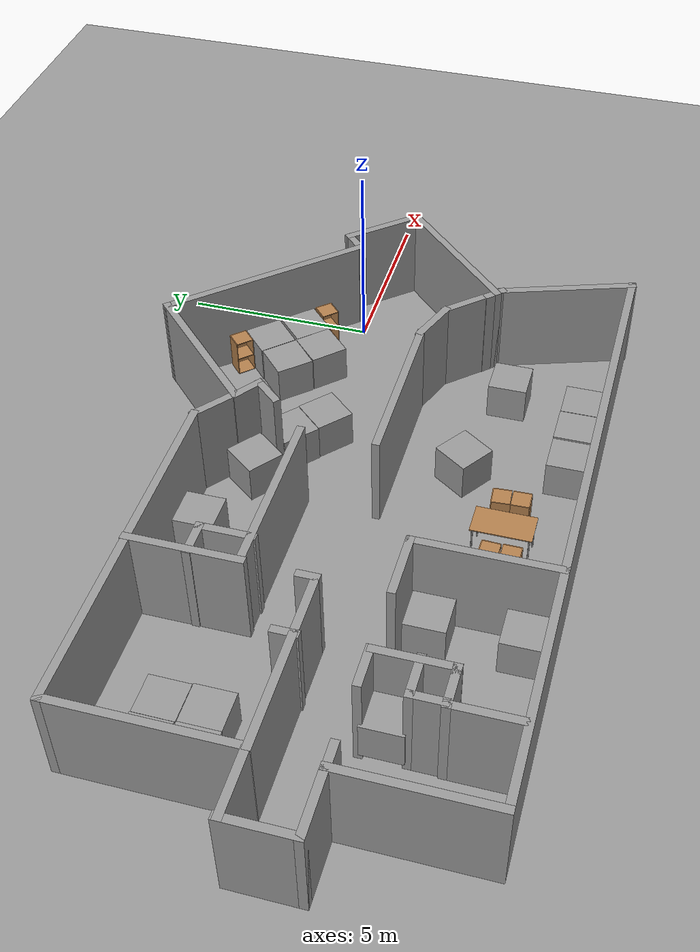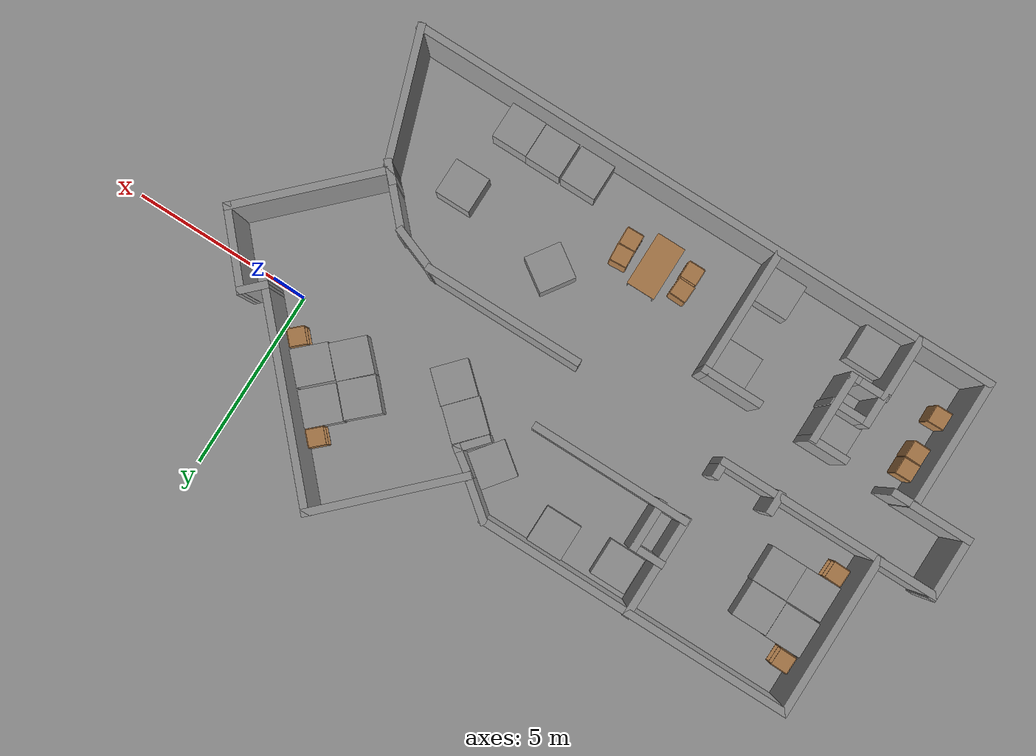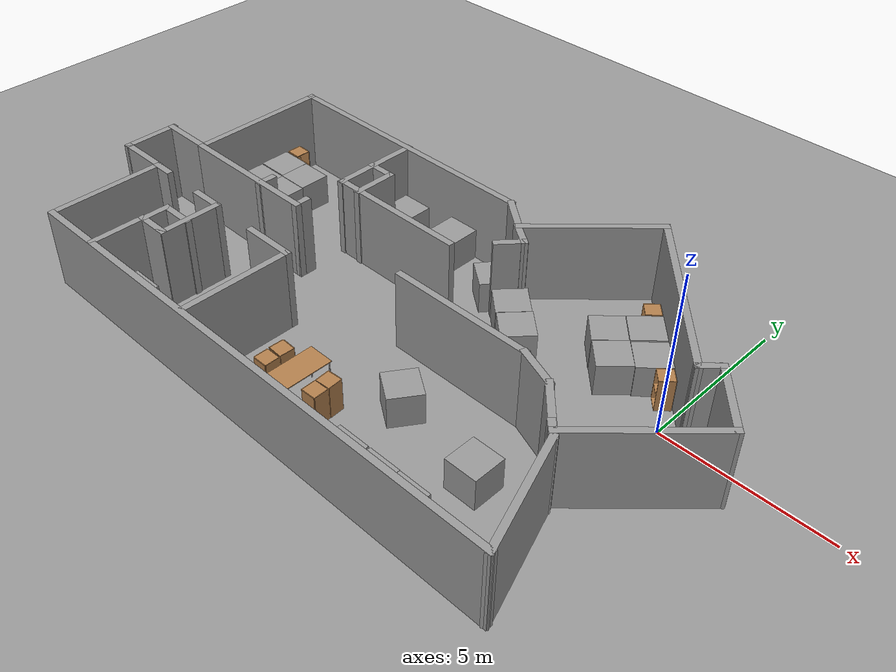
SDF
<sdf version="1.4">
 <world name="default">
  <light name="sun" type="directional">
   <pose>0 0 10 0 -0 0</pose>
   <diffuse>0.8 0.8 0.8 1</diffuse>
   <specular>0.2 0.2 0.2 1</specular>
   <attenuation>
    <range>1000</range>
    <constant>0.9</constant>
    <linear>0.01</linear>
    <quadratic>0.001</quadratic>
   </attenuation>
   <direction>0.5 0.1 -0.9</direction>
  </light>
  <scene><ambient>0.4 0.4 0.4 1</ambient><background>0.7 0.7 0.7 1</background><shadows>1</shadows></scene>
  <physics type="ode">
   <max_step_size>0.01</max_step_size>
   <real_time_factor>1</real_time_factor>
   <real_time_update_rate>100</real_time_update_rate>
   <gravity>0 0 -9.8</gravity>
  </physics>
  <model name="ground_plane_0">
   <static>1</static>
   <link name="link">
    <collision name="collision">
     <geometry><plane><normal>0 0 1</normal><size>100 100</size></plane></geometry>
     <surface><friction><ode><mu>100</mu><mu2>50</mu2></ode></friction></surface>
    </collision>
    <visual name="visual">
     <cast_shadows>0</cast_shadows>
     <geometry><plane><normal>0 0 1</normal><size>100 100</size></plane></geometry>
     <material>
      <script><uri>file://media/materials/scripts/gazebo.material</uri><name>Gazebo/Grey</name></script>
     </material>
    </visual>
    <velocity_decay><linear>0</linear><angular>0</angular></velocity_decay>
   </link>
   <pose>0.497681 0 0 0 -0 0</pose>
  </model>
  <spherical_coordinates>
   <surface_model>EARTH_WGS84</surface_model>
   <latitude_deg>0</latitude_deg>
   <longitude_deg>0</longitude_deg>
   <elevation>0</elevation>
   <heading_deg>0</heading_deg>
  </spherical_coordinates>
  <model name="roy4">
   <link name="Wall_0">
    <collision name="Wall_0_Collision">
     <geometry><box><size>1.81822 0.2 2.5</size></box></geometry>
     <pose>0 0 1.25 0 -0 0</pose>
    </collision>
    <visual name="Wall_0_Visual">
     <pose>0 0 1.25 0 -0 0</pose>
     <geometry><box><size>1.81822 0.2 2.5</size></box></geometry>
     <material>
      <script><uri>file://media/materials/scripts/gazebo.material</uri><name>Gazebo/Grey</name></script>
     </material>
    </visual>
    <velocity_decay><linear>0</linear><angular>0</angular></velocity_decay>
    <pose>-18.2093 -1.86186 0 0 0 -1.5708</pose>
   </link>
   <link name="Wall_1">
    <collision name="Wall_1_Collision">
     <geometry><box><size>1.73731 0.2 2.5</size></box></geometry>
     <pose>0 0 1.25 0 -0 0</pose>
    </collision>
    <visual name="Wall_1_Visual">
     <pose>0 0 1.25 0 -0 0</pose>
     <geometry><box><size>1.73731 0.2 2.5</size></box></geometry>
     <material>
      <script><uri>file://media/materials/scripts/gazebo.material</uri><name>Gazebo/Grey</name></script>
     </material>
    </visual>
    <velocity_decay><linear>0</linear><angular>0</angular></velocity_decay>
    <pose>-17.4407 -2.67097 0 0 -0 0</pose>
   </link>
   <link name="Wall_10">
    <collision name="Wall_10_Collision">
     <geometry><box><size>4.52875 0.2 2.5</size></box></geometry>
     <pose>0 0 1.25 0 -0 0</pose>
    </collision>
    <visual name="Wall_10_Visual">
     <pose>0 0 1.25 0 -0 0</pose>
     <geometry><box><size>4.52875 0.2 2.5</size></box></geometry>
     <material>
      <script><uri>file://media/materials/scripts/gazebo.material</uri><name>Gazebo/Grey</name></script>
     </material>
    </visual>
    <velocity_decay><linear>0</linear><angular>0</angular></velocity_decay>
    <pose>-16.6315 1.07117 0 0 -0 1.5708</pose>
   </link>
   <link name="Wall_11">
    <collision name="Wall_11_Collision">
     <geometry><box><size>8.81704 0.2 2.5</size></box></geometry>
     <pose>0 0 1.25 0 -0 0</pose>
    </collision>
    <visual name="Wall_11_Visual">
     <pose>0 0 1.25 0 -0 0</pose>
     <geometry><box><size>8.81704 0.2 2.5</size></box></geometry>
     <material>
      <script><uri>file://media/materials/scripts/gazebo.material</uri><name>Gazebo/Grey</name></script>
     </material>
    </visual>
    <velocity_decay><linear>0</linear><angular>0</angular></velocity_decay>
    <pose>-12.323 3.23554 0 0 -0 0</pose>
   </link>
   <link name="Wall_12">
    <collision name="Wall_12_Collision">
     <geometry><box><size>1.34948 0.2 2.5</size></box></geometry>
     <pose>0 0 1.25 0 -0 0</pose>
    </collision>
    <visual name="Wall_12_Visual">
     <pose>0 0 1.25 0 -0 0</pose>
     <geometry><box><size>1.34948 0.2 2.5</size></box></geometry>
     <material>
      <script><uri>file://media/materials/scripts/gazebo.material</uri><name>Gazebo/Grey</name></script>
     </material>
    </visual>
    <velocity_decay><linear>0</linear><angular>0</angular></velocity_decay>
    <pose>-7.56237 2.88072 0 0 0 -0.665383</pose>
   </link>
   <link name="Wall_13">
    <collision name="Wall_13_Collision">
     <geometry><box><size>4.25051 0.2 2.5</size></box></geometry>
     <pose>0 0 1.25 0 -0 0</pose>
    </collision>
    <visual name="Wall_13_Visual">
     <pose>0 0 1.25 0 -0 0</pose>
     <geometry><box><size>4.25051 0.2 2.5</size></box></geometry>
     <material>
      <script><uri>file://media/materials/scripts/gazebo.material</uri><name>Gazebo/Grey</name></script>
     </material>
    </visual>
    <velocity_decay><linear>0</linear><angular>0</angular></velocity_decay>
    <pose>-5.67816 3.95797 0 0 -0 0.785398</pose>
   </link>
   <link name="Wall_14">
    <collision name="Wall_14_Collision">
     <geometry><box><size>5.8449 0.2 2.5</size></box></geometry>
     <pose>0 0 1.25 0 -0 0</pose>
    </collision>
    <visual name="Wall_14_Visual">
     <pose>0 0 1.25 0 -0 0</pose>
     <geometry><box><size>5.8449 0.2 2.5</size></box></geometry>
     <material>
      <script><uri>file://media/materials/scripts/gazebo.material</uri><name>Gazebo/Grey</name></script>
     </material>
    </visual>
    <velocity_decay><linear>0</linear><angular>0</angular></velocity_decay>
    <pose>-2.32907 3.3185 0 0 0 -0.824116</pose>
   </link>
   <link name="Wall_15">
    <collision name="Wall_15_Collision">
     <geometry><box><size>0.805312 0.2 2.5</size></box></geometry>
     <pose>0 0 1.25 0 -0 0</pose>
    </collision>
    <visual name="Wall_15_Visual">
     <pose>0 0 1.25 0 -0 0</pose>
     <geometry><box><size>0.805312 0.2 2.5</size></box></geometry>
     <material>
      <script><uri>file://media/materials/scripts/gazebo.material</uri><name>Gazebo/Grey</name></script>
     </material>
    </visual>
    <velocity_decay><linear>0</linear><angular>0</angular></velocity_decay>
    <pose>-0.198034 1.46098 0 0 -0 0.785398</pose>
   </link>
   <link name="Wall_16">
    <collision name="Wall_16_Collision">
     <geometry><box><size>2.30527 0.2 2.5</size></box></geometry>
     <pose>0 0 1.25 0 -0 0</pose>
    </collision>
    <visual name="Wall_16_Visual">
     <pose>0 0 1.25 0 -0 0</pose>
     <geometry><box><size>2.30527 0.2 2.5</size></box></geometry>
     <material>
      <script><uri>file://media/materials/scripts/gazebo.material</uri><name>Gazebo/Grey</name></script>
     </material>
    </visual>
    <velocity_decay><linear>0</linear><angular>0</angular></velocity_decay>
    <pose>0.716942 0.889618 0 0 0 -0.842126</pose>
   </link>
   <link name="Wall_17">
    <collision name="Wall_17_Collision">
     <geometry><box><size>4.28091 0.2 2.5</size></box></geometry>
     <pose>0 0 1.25 0 -0 0</pose>
    </collision>
    <visual name="Wall_17_Visual">
     <pose>0 0 1.25 0 -0 0</pose>
     <geometry><box><size>4.28091 0.2 2.5</size></box></geometry>
     <material>
      <script><uri>file://media/materials/scripts/gazebo.material</uri><name>Gazebo/Grey</name></script>
     </material>
    </visual>
    <velocity_decay><linear>0</linear><angular>0</angular></velocity_decay>
    <pose>-0.024913 -1.33858 0 0 0 -2.35619</pose>
   </link>
   <link name="Wall_18">
    <collision name="Wall_18_Collision">
     <geometry><box><size>0.478047 0.2 2.5</size></box></geometry>
     <pose>0 0 1.25 0 -0 0</pose>
    </collision>
    <visual name="Wall_18_Visual">
     <pose>0 0 1.25 0 -0 0</pose>
     <geometry><box><size>0.478047 0.2 2.5</size></box></geometry>
     <material>
      <script><uri>file://media/materials/scripts/gazebo.material</uri><name>Gazebo/Grey</name></script>
     </material>
    </visual>
    <velocity_decay><linear>0</linear><angular>0</angular></velocity_decay>
    <pose>-1.56604 -2.68309 0 0 -0 2.35619</pose>
   </link>
   <link name="Wall_2">
    <collision name="Wall_2_Collision">
     <geometry><box><size>3.71963 0.2 2.5</size></box></geometry>
     <pose>0 0 1.25 0 -0 0</pose>
    </collision>
    <visual name="Wall_2_Visual">
     <pose>0 0 1.25 0 -0 0</pose>
     <geometry><box><size>3.71963 0.2 2.5</size></box></geometry>
     <material>
      <script><uri>file://media/materials/scripts/gazebo.material</uri><name>Gazebo/Grey</name></script>
     </material>
    </visual>
    <velocity_decay><linear>0</linear><angular>0</angular></velocity_decay>
    <pose>-16.672 -4.43079 0 0 0 -1.5708</pose>
   </link>
   <link name="Wall_20">
    <collision name="Wall_20_Collision">
     <geometry><box><size>0.725923 0.2 2.5</size></box></geometry>
     <pose>0 0 1.25 0 -0 0</pose>
    </collision>
    <visual name="Wall_20_Visual">
     <pose>0 0 1.25 0 -0 0</pose>
     <geometry><box><size>0.725923 0.2 2.5</size></box></geometry>
     <material>
      <script><uri>file://media/materials/scripts/gazebo.material</uri><name>Gazebo/Grey</name></script>
     </material>
    </visual>
    <velocity_decay><linear>0</linear><angular>0</angular></velocity_decay>
    <pose>-16.4029 -2.68936 0 0 -0 0</pose>
   </link>
   <link name="Wall_22">
    <collision name="Wall_22_Collision">
     <geometry><box><size>1.09002 0.2 2.5</size></box></geometry>
     <pose>0 0 1.25 0 -0 0</pose>
    </collision>
    <visual name="Wall_22_Visual">
     <pose>0 0 1.25 0 -0 0</pose>
     <geometry><box><size>1.09002 0.2 2.5</size></box></geometry>
     <material>
      <script><uri>file://media/materials/scripts/gazebo.material</uri><name>Gazebo/Grey</name></script>
     </material>
    </visual>
    <velocity_decay><linear>0</linear><angular>0</angular></velocity_decay>
    <pose>-14.1981 -2.72981 0 0 -0 0</pose>
   </link>
   <link name="Wall_24">
    <collision name="Wall_24_Collision">
     <geometry><box><size>1.98005 0.2 2.5</size></box></geometry>
     <pose>0 0 1.25 0 -0 0</pose>
    </collision>
    <visual name="Wall_24_Visual">
     <pose>0 0 1.25 0 -0 0</pose>
     <geometry><box><size>1.98005 0.2 2.5</size></box></geometry>
     <material>
      <script><uri>file://media/materials/scripts/gazebo.material</uri><name>Gazebo/Grey</name></script>
     </material>
    </visual>
    <velocity_decay><linear>0</linear><angular>0</angular></velocity_decay>
    <pose>-13.7531 -3.66029 0 0 0 -1.5708</pose>
   </link>
   <link name="Wall_25">
    <collision name="Wall_25_Collision">
     <geometry><box><size>0.321367 0.2 2.5</size></box></geometry>
     <pose>0 0 1.25 0 -0 0</pose>
    </collision>
    <visual name="Wall_25_Visual">
     <pose>0 0 1.25 0 -0 0</pose>
     <geometry><box><size>0.321367 0.2 2.5</size></box></geometry>
     <material>
      <script><uri>file://media/materials/scripts/gazebo.material</uri><name>Gazebo/Grey</name></script>
     </material>
    </visual>
    <velocity_decay><linear>0</linear><angular>0</angular></velocity_decay>
    <pose>-13.8138 -4.55032 0 0 -0 3.14159</pose>
   </link>
   <link name="Wall_27">
    <collision name="Wall_27_Collision">
     <geometry><box><size>1.09002 0.2 2.5</size></box></geometry>
     <pose>0 0 1.25 0 -0 0</pose>
    </collision>
    <visual name="Wall_27_Visual">
     <pose>0 0 1.25 0 -0 0</pose>
     <geometry><box><size>1.09002 0.2 2.5</size></box></geometry>
     <material>
      <script><uri>file://media/materials/scripts/gazebo.material</uri><name>Gazebo/Grey</name></script>
     </material>
    </visual>
    <velocity_decay><linear>0</linear><angular>0</angular></velocity_decay>
    <pose>-14.2386 -4.55032 0 0 -0 3.14159</pose>
   </link>
   <link name="Wall_28">
    <collision name="Wall_28_Collision">
     <geometry><box><size>1.81822 0.2 2.5</size></box></geometry>
     <pose>0 0 1.25 0 -0 0</pose>
    </collision>
    <visual name="Wall_28_Visual">
     <pose>0 0 1.25 0 -0 0</pose>
     <geometry><box><size>1.81822 0.2 2.5</size></box></geometry>
     <material>
      <script><uri>file://media/materials/scripts/gazebo.material</uri><name>Gazebo/Grey</name></script>
     </material>
    </visual>
    <velocity_decay><linear>0</linear><angular>0</angular></velocity_decay>
    <pose>-14.6836 -5.35943 0 0 0 -1.5708</pose>
   </link>
   <link name="Wall_3">
    <collision name="Wall_3_Collision">
     <geometry><box><size>16.6654 0.2 2.5</size></box></geometry>
     <pose>0 0 1.25 0 -0 0</pose>
    </collision>
    <visual name="Wall_3_Visual">
     <pose>0 0 1.25 0 -0 0</pose>
     <geometry><box><size>16.6654 0.2 2.5</size></box></geometry>
     <material>
      <script><uri>file://media/materials/scripts/gazebo.material</uri><name>Gazebo/Grey</name></script>
     </material>
    </visual>
    <velocity_decay><linear>0</linear><angular>0</angular></velocity_decay>
    <pose>-8.43929 -6.19061 0 0 -0 0</pose>
   </link>
   <link name="Wall_30">
    <collision name="Wall_30_Collision">
     <geometry><box><size>0.9282 0.2 2.5</size></box></geometry>
     <pose>0 0 1.25 0 -0 0</pose>
    </collision>
    <visual name="Wall_30_Visual">
     <pose>0 0 1.25 0 -0 0</pose>
     <geometry><box><size>0.9282 0.2 2.5</size></box></geometry>
     <material>
      <script><uri>file://media/materials/scripts/gazebo.material</uri><name>Gazebo/Grey</name></script>
     </material>
    </visual>
    <velocity_decay><linear>0</linear><angular>0</angular></velocity_decay>
    <pose>-14.6431 -4.14576 0 0 -0 1.5708</pose>
   </link>
   <link name="Wall_31">
    <collision name="Wall_31_Collision">
     <geometry><box><size>1.13048 0.2 2.5</size></box></geometry>
     <pose>0 0 1.25 0 -0 0</pose>
    </collision>
    <visual name="Wall_31_Visual">
     <pose>0 0 1.25 0 -0 0</pose>
     <geometry><box><size>1.13048 0.2 2.5</size></box></geometry>
     <material>
      <script><uri>file://media/materials/scripts/gazebo.material</uri><name>Gazebo/Grey</name></script>
     </material>
    </visual>
    <velocity_decay><linear>0</linear><angular>0</angular></velocity_decay>
    <pose>-14.1779 -3.78166 0 0 -0 0</pose>
   </link>
   <link name="Wall_33">
    <collision name="Wall_33_Collision">
     <geometry><box><size>1.69686 0.2 2.5</size></box></geometry>
     <pose>0 0 1.25 0 -0 0</pose>
    </collision>
    <visual name="Wall_33_Visual">
     <pose>0 0 1.25 0 -0 0</pose>
     <geometry><box><size>1.69686 0.2 2.5</size></box></geometry>
     <material>
      <script><uri>file://media/materials/scripts/gazebo.material</uri><name>Gazebo/Grey</name></script>
     </material>
    </visual>
    <velocity_decay><linear>0</linear><angular>0</angular></velocity_decay>
    <pose>-11.3864 -2.77027 0 0 -0 0</pose>
   </link>
   <link name="Wall_34">
    <collision name="Wall_34_Collision">
     <geometry><box><size>3.59827 0.2 2.5</size></box></geometry>
     <pose>0 0 1.25 0 -0 0</pose>
    </collision>
    <visual name="Wall_34_Visual">
     <pose>0 0 1.25 0 -0 0</pose>
     <geometry><box><size>3.59827 0.2 2.5</size></box></geometry>
     <material>
      <script><uri>file://media/materials/scripts/gazebo.material</uri><name>Gazebo/Grey</name></script>
     </material>
    </visual>
    <velocity_decay><linear>0</linear><angular>0</angular></velocity_decay>
    <pose>-10.638 -4.4694 0 0 0 -1.5708</pose>
   </link>
   <link name="Wall_36">
    <collision name="Wall_36_Collision">
     <geometry><box><size>4.60966 0.2 2.5</size></box></geometry>
     <pose>0 0 1.25 0 -0 0</pose>
    </collision>
    <visual name="Wall_36_Visual">
     <pose>0 0 1.25 0 -0 0</pose>
     <geometry><box><size>4.60966 0.2 2.5</size></box></geometry>
     <material>
      <script><uri>file://media/materials/scripts/gazebo.material</uri><name>Gazebo/Grey</name></script>
     </material>
    </visual>
    <velocity_decay><linear>0</linear><angular>0</angular></velocity_decay>
    <pose>-14.4206 -1.11159 0 0 -0 0</pose>
   </link>
   <link name="Wall_37">
    <collision name="Wall_37_Collision">
     <geometry><box><size>0.5641 0.2 2.5</size></box></geometry>
     <pose>0 0 1.25 0 -0 0</pose>
    </collision>
    <visual name="Wall_37_Visual">
     <pose>0 0 1.25 0 -0 0</pose>
     <geometry><box><size>0.5641 0.2 2.5</size></box></geometry>
     <material>
      <script><uri>file://media/materials/scripts/gazebo.material</uri><name>Gazebo/Grey</name></script>
     </material>
    </visual>
    <velocity_decay><linear>0</linear><angular>0</angular></velocity_decay>
    <pose>-12.2158 -0.929541 0 0 -0 1.5708</pose>
   </link>
   <link name="Wall_39">
    <collision name="Wall_39_Collision">
     <geometry><box><size>0.645011 0.2 2.5</size></box></geometry>
     <pose>0 0 1.25 0 -0 0</pose>
    </collision>
    <visual name="Wall_39_Visual">
     <pose>0 0 1.25 0 -0 0</pose>
     <geometry><box><size>0.645011 0.2 2.5</size></box></geometry>
     <material>
      <script><uri>file://media/materials/scripts/gazebo.material</uri><name>Gazebo/Grey</name></script>
     </material>
    </visual>
    <velocity_decay><linear>0</linear><angular>0</angular></velocity_decay>
    <pose>-13.7935 -0.929541 0 0 -0 1.5708</pose>
   </link>
   <link name="Wall_4">
    <collision name="Wall_4_Collision">
     <geometry><box><size>3.66716 0.2 2.5</size></box></geometry>
     <pose>0 0 1.25 0 -0 0</pose>
    </collision>
    <visual name="Wall_4_Visual">
     <pose>0 0 1.25 0 -0 0</pose>
     <geometry><box><size>3.66716 0.2 2.5</size></box></geometry>
     <material>
      <script><uri>file://media/materials/scripts/gazebo.material</uri><name>Gazebo/Grey</name></script>
     </material>
    </visual>
    <velocity_decay><linear>0</linear><angular>0</angular></velocity_decay>
    <pose>-0.772961 -4.55216 0 0 -0 1.90362</pose>
   </link>
   <link name="Wall_41">
    <collision name="Wall_41_Collision">
     <geometry><box><size>2.87038 0.2 2.5</size></box></geometry>
     <pose>0 0 1.25 0 -0 0</pose>
    </collision>
    <visual name="Wall_41_Visual">
     <pose>0 0 1.25 0 -0 0</pose>
     <geometry><box><size>2.87038 0.2 2.5</size></box></geometry>
     <material>
      <script><uri>file://media/materials/scripts/gazebo.material</uri><name>Gazebo/Grey</name></script>
     </material>
    </visual>
    <velocity_decay><linear>0</linear><angular>0</angular></velocity_decay>
    <pose>-12.1753 1.92242 0 0 0 -1.5708</pose>
   </link>
   <link name="Wall_5">
    <collision name="Wall_5_Collision">
     <geometry><box><size>1.91734 0.2 2.5</size></box></geometry>
     <pose>0 0 1.25 0 -0 0</pose>
    </collision>
    <visual name="Wall_5_Visual">
     <pose>0 0 1.25 0 -0 0</pose>
     <geometry><box><size>1.91734 0.2 2.5</size></box></geometry>
     <material>
      <script><uri>file://media/materials/scripts/gazebo.material</uri><name>Gazebo/Grey</name></script>
     </material>
    </visual>
    <velocity_decay><linear>0</linear><angular>0</angular></velocity_decay>
    <pose>-1.92595 -2.28665 0 0 -0 2.32287</pose>
   </link>
   <link name="Wall_50">
    <collision name="Wall_50_Collision">
     <geometry><box><size>4.44784 0.2 2.5</size></box></geometry>
     <pose>0 0 1.25 0 -0 0</pose>
    </collision>
    <visual name="Wall_50_Visual">
     <pose>0 0 1.25 0 -0 0</pose>
     <geometry><box><size>4.44784 0.2 2.5</size></box></geometry>
     <material>
      <script><uri>file://media/materials/scripts/gazebo.material</uri><name>Gazebo/Grey</name></script>
     </material>
    </visual>
    <velocity_decay><linear>0</linear><angular>0</angular></velocity_decay>
    <pose>-10.0252 0.613532 0 0 -0 0</pose>
   </link>
   <link name="Wall_52">
    <collision name="Wall_52_Collision">
     <geometry><box><size>0.932023 0.2 2.5</size></box></geometry>
     <pose>0 0 1.25 0 -0 0</pose>
    </collision>
    <visual name="Wall_52_Visual">
     <pose>0 0 1.25 0 -0 0</pose>
     <geometry><box><size>0.932023 0.2 2.5</size></box></geometry>
     <material>
      <script><uri>file://media/materials/scripts/gazebo.material</uri><name>Gazebo/Grey</name></script>
     </material>
    </visual>
    <velocity_decay><linear>0</linear><angular>0</angular></velocity_decay>
    <pose>-6.83392 2.29891 0 0 0 -0.614663</pose>
   </link>
   <link name="Wall_53">
    <collision name="Wall_53_Collision">
     <geometry><box><size>0.947911 0.2 2.5</size></box></geometry>
     <pose>0 0 1.25 0 -0 0</pose>
    </collision>
    <visual name="Wall_53_Visual">
     <pose>0 0 1.25 0 -0 0</pose>
     <geometry><box><size>0.947911 0.2 2.5</size></box></geometry>
     <material>
      <script><uri>file://media/materials/scripts/gazebo.material</uri><name>Gazebo/Grey</name></script>
     </material>
    </visual>
    <velocity_decay><linear>0</linear><angular>0</angular></velocity_decay>
    <pose>-6.78115 1.80641 0 0 0 -2.28963</pose>
   </link>
   <link name="Wall_55">
    <collision name="Wall_55_Collision">
     <geometry><box><size>0.938754 0.2 2.5</size></box></geometry>
     <pose>0 0 1.25 0 -0 0</pose>
    </collision>
    <visual name="Wall_55_Visual">
     <pose>0 0 1.25 0 -0 0</pose>
     <geometry><box><size>0.938754 0.2 2.5</size></box></geometry>
     <material>
      <script><uri>file://media/materials/scripts/gazebo.material</uri><name>Gazebo/Grey</name></script>
     </material>
    </visual>
    <velocity_decay><linear>0</linear><angular>0</angular></velocity_decay>
    <pose>-11.8293 1.80641 0 0 -0 0</pose>
   </link>
   <link name="Wall_56">
    <collision name="Wall_56_Collision">
     <geometry><box><size>1.43126 0.2 2.5</size></box></geometry>
     <pose>0 0 1.25 0 -0 0</pose>
    </collision>
    <visual name="Wall_56_Visual">
     <pose>0 0 1.25 0 -0 0</pose>
     <geometry><box><size>1.43126 0.2 2.5</size></box></geometry>
     <material>
      <script><uri>file://media/materials/scripts/gazebo.material</uri><name>Gazebo/Grey</name></script>
     </material>
    </visual>
    <velocity_decay><linear>0</linear><angular>0</angular></velocity_decay>
    <pose>-11.4599 1.19078 0 0 0 -1.5708</pose>
   </link>
   <link name="Wall_6">
    <collision name="Wall_6_Collision">
     <geometry><box><size>1.36481 0.2 2.5</size></box></geometry>
     <pose>0 0 1.25 0 -0 0</pose>
    </collision>
    <visual name="Wall_6_Visual">
     <pose>0 0 1.25 0 -0 0</pose>
     <geometry><box><size>1.36481 0.2 2.5</size></box></geometry>
     <material>
      <script><uri>file://media/materials/scripts/gazebo.material</uri><name>Gazebo/Grey</name></script>
     </material>
    </visual>
    <velocity_decay><linear>0</linear><angular>0</angular></velocity_decay>
    <pose>-3.0587 -1.45731 0 0 -0 2.78689</pose>
   </link>
   <link name="Wall_7">
    <collision name="Wall_7_Collision">
     <geometry><box><size>4.44784 0.2 2.5</size></box></geometry>
     <pose>0 0 1.25 0 -0 0</pose>
    </collision>
    <visual name="Wall_7_Visual">
     <pose>0 0 1.25 0 -0 0</pose>
     <geometry><box><size>4.44784 0.2 2.5</size></box></geometry>
     <material>
      <script><uri>file://media/materials/scripts/gazebo.material</uri><name>Gazebo/Grey</name></script>
     </material>
    </visual>
    <velocity_decay><linear>0</linear><angular>0</angular></velocity_decay>
    <pose>-5.72877 -1.25503 0 0 -0 3.14159</pose>
   </link>
   <link name="Wall_9">
    <collision name="Wall_9_Collision">
     <geometry><box><size>1.77777 0.2 2.5</size></box></geometry>
     <pose>0 0 1.25 0 -0 0</pose>
    </collision>
    <visual name="Wall_9_Visual">
     <pose>0 0 1.25 0 -0 0</pose>
     <geometry><box><size>1.77777 0.2 2.5</size></box></geometry>
     <material>
      <script><uri>file://media/materials/scripts/gazebo.material</uri><name>Gazebo/Grey</name></script>
     </material>
    </visual>
    <velocity_decay><linear>0</linear><angular>0</angular></velocity_decay>
    <pose>-17.4204 -1.09321 0 0 -0 0</pose>
   </link>
   <static>1</static>
   <pose>1 -1 0 0 -0 0</pose>
  </model>
  <model name="unit_box_10">
   <pose>-13.3082 -4.25233 0.726005 0 -0 0.000186</pose>
   <link name="link">
    <inertial>
     <mass>1</mass>
     <inertia><ixx>1</ixx><ixy>0</ixy><ixz>0</ixz><iyy>1</iyy><iyz>0</iyz><izz>1</izz></inertia>
    </inertial>
    <collision name="collision"><geometry><box><size>0.908301 0.843927 1.45201</size></box></geometry></collision>
    <visual name="visual">
     <geometry><box><size>1 1 1</size></box></geometry>
     <material>
      <script><uri>file://media/materials/scripts/gazebo.material</uri><name>Gazebo/Grey</name></script>
     </material>
    </visual>
    <velocity_decay><linear>0</linear><angular>0</angular></velocity_decay>
   </link>
   <static>0</static>
  </model>
  <model name="table">
   <static>1</static>
   <link name="link">
    <collision name="surface">
     <pose>0 0 1 0 -0 0</pose>
     <geometry><box><size>1.5 0.8 0.03</size></box></geometry>
     <surface><friction><ode><mu>0.6</mu><mu2>0.6</mu2></ode></friction></surface>
    </collision>
    <visual name="visual1">
     <pose>0 0 1 0 -0 0</pose>
     <geometry><box><size>1.5 0.8 0.03</size></box></geometry>
     <material>
      <script><uri>file://media/materials/scripts/gazebo.material</uri><name>Gazebo/Wood</name></script>
     </material>
    </visual>
    <collision name="front_left_leg">
     <pose>0.68 0.38 0.5 0 -0 0</pose>
     <geometry><cylinder><radius>0.02</radius><length>1</length></cylinder></geometry>
    </collision>
    <visual name="front_left_leg">
     <pose>0.68 0.38 0.5 0 -0 0</pose>
     <geometry><cylinder><radius>0.02</radius><length>1</length></cylinder></geometry>
     <material>
      <script><uri>file://media/materials/scripts/gazebo.material</uri><name>Gazebo/Grey</name></script>
     </material>
    </visual>
    <collision name="front_right_leg">
     <pose>0.68 -0.38 0.5 0 -0 0</pose>
     <geometry><cylinder><radius>0.02</radius><length>1</length></cylinder></geometry>
    </collision>
    <visual name="front_right_leg">
     <pose>0.68 -0.38 0.5 0 -0 0</pose>
     <geometry><cylinder><radius>0.02</radius><length>1</length></cylinder></geometry>
     <material>
      <script><uri>file://media/materials/scripts/gazebo.material</uri><name>Gazebo/Grey</name></script>
     </material>
    </visual>
    <collision name="back_right_leg">
     <pose>-0.68 -0.38 0.5 0 -0 0</pose>
     <geometry><cylinder><radius>0.02</radius><length>1</length></cylinder></geometry>
    </collision>
    <visual name="back_right_leg">
     <pose>-0.68 -0.38 0.5 0 -0 0</pose>
     <geometry><cylinder><radius>0.02</radius><length>1</length></cylinder></geometry>
     <material>
      <script><uri>file://media/materials/scripts/gazebo.material</uri><name>Gazebo/Grey</name></script>
     </material>
    </visual>
    <collision name="back_left_leg">
     <pose>-0.68 0.38 0.5 0 -0 0</pose>
     <geometry><cylinder><radius>0.02</radius><length>1</length></cylinder></geometry>
    </collision>
    <visual name="back_left_leg">
     <pose>-0.68 0.38 0.5 0 -0 0</pose>
     <geometry><cylinder><radius>0.02</radius><length>1</length></cylinder></geometry>
     <material>
      <script><uri>file://media/materials/scripts/gazebo.material</uri><name>Gazebo/Grey</name></script>
     </material>
    </visual>
    <velocity_decay><linear>0</linear><angular>0</angular></velocity_decay>
   </link>
   <pose>-7.25274 -5.46109 0 0 0 -1.57106</pose>
  </model>
  <model name="unit_box_1_0">
   <pose>-15.0297 0.464499 0.5 0 -0 -0.002706</pose>
   <link name="link">
    <inertial>
     <mass>1</mass>
     <inertia><ixx>1</ixx><ixy>0</ixy><ixz>0</ixz><iyy>1</iyy><iyz>0</iyz><izz>1</izz></inertia>
    </inertial>
    <collision name="collision"><geometry><box><size>1 1 1</size></box></geometry></collision>
    <visual name="visual">
     <geometry><box><size>1 1 1</size></box></geometry>
     <material>
      <script><uri>file://media/materials/scripts/gazebo.material</uri><name>Gazebo/Grey</name></script>
     </material>
    </visual>
    <velocity_decay><linear>0</linear><angular>0</angular></velocity_decay>
   </link>
   <static>0</static>
  </model>
  <model name="unit_box_3_0">
   <pose>-14.0262 0.442956 0.5 0 0 -0.004674</pose>
   <link name="link">
    <inertial>
     <mass>1</mass>
     <inertia><ixx>1</ixx><ixy>0</ixy><ixz>0</ixz><iyy>1</iyy><iyz>0</iyz><izz>1</izz></inertia>
    </inertial>
    <collision name="collision"><geometry><box><size>1 1 1</size></box></geometry></collision>
    <visual name="visual">
     <geometry><box><size>1 1 1</size></box></geometry>
     <material>
      <script><uri>file://media/materials/scripts/gazebo.material</uri><name>Gazebo/Grey</name></script>
     </material>
    </visual>
    <velocity_decay><linear>0</linear><angular>0</angular></velocity_decay>
   </link>
   <static>0</static>
  </model>
  <model name="unit_box_4">
   <pose>-15 -0.567665 0.5 -0 -0 -0</pose>
   <link name="link">
    <inertial>
     <mass>1</mass>
     <inertia><ixx>1</ixx><ixy>0</ixy><ixz>0</ixz><iyy>1</iyy><iyz>0</iyz><izz>1</izz></inertia>
    </inertial>
    <collision name="collision"><geometry><box><size>1 1 1</size></box></geometry></collision>
    <visual name="visual">
     <geometry><box><size>1 1 1</size></box></geometry>
     <material>
      <script><uri>file://media/materials/scripts/gazebo.material</uri><name>Gazebo/Grey</name></script>
     </material>
    </visual>
    <velocity_decay><linear>0</linear><angular>0</angular></velocity_decay>
   </link>
   <static>0</static>
  </model>
  <model name="unit_box_5_0">
   <pose>-14 -0.568383 0.5 0 -0 0</pose>
   <link name="link">
    <inertial>
     <mass>1</mass>
     <inertia><ixx>1</ixx><ixy>0</ixy><ixz>0</ixz><iyy>1</iyy><iyz>0</iyz><izz>1</izz></inertia>
    </inertial>
    <collision name="collision"><geometry><box><size>1 1 1</size></box></geometry></collision>
    <visual name="visual">
     <geometry><box><size>1 1 1</size></box></geometry>
     <material>
      <script><uri>file://media/materials/scripts/gazebo.material</uri><name>Gazebo/Grey</name></script>
     </material>
    </visual>
    <velocity_decay><linear>0</linear><angular>0</angular></velocity_decay>
   </link>
   <static>0</static>
  </model>
  <model name="cabinet">
   <static>1</static>
   <link name="cabinet_bottom_plate">
    <inertial>
     <pose>0 0 -1 0 -0 0</pose>
     <inertia><ixx>2.05</ixx><ixy>0</ixy><ixz>0</ixz><iyy>2.05</iyy><iyz>0</iyz><izz>2.05</izz></inertia>
     <mass>25</mass>
    </inertial>
    <collision name="cabinet_bottom_plate_geom">
     <pose>0 0 0.01 0 -0 0</pose>
     <geometry><box><size>0.45 0.45 0.02</size></box></geometry>
    </collision>
    <visual name="cabinet_bottom_plate_geom_visual">
     <pose>0 0 0.01 0 -0 0</pose>
     <geometry><box><size>0.45 0.45 0.02</size></box></geometry>
     <material>
      <script><uri>file://media/materials/scripts/gazebo.material</uri><name>Gazebo/Wood</name></script>
     </material>
    </visual>
    <collision name="cabinet_bottom_plate_geom_cabinet_back_plate">
     <pose>0.235 0 0.51 0 -0 0</pose>
     <geometry><box><size>0.02 0.45 1.02</size></box></geometry>
    </collision>
    <visual name="cabinet_bottom_plate_geom_cabinet_back_plate_visual">
     <pose>0.235 0 0.51 0 -0 0</pose>
     <geometry><box><size>0.02 0.45 1.02</size></box></geometry>
     <material>
      <script><uri>file://media/materials/scripts/gazebo.material</uri><name>Gazebo/Wood</name></script>
     </material>
    </visual>
    <collision name="cabinet_bottom_plate_geom_cabinet_left_plate">
     <pose>0 0.235 0.51 0 -0 0</pose>
     <geometry><box><size>0.45 0.02 1.02</size></box></geometry>
    </collision>
    <visual name="cabinet_bottom_plate_geom_cabinet_left_plate_visual">
     <pose>0 0.235 0.51 0 -0 0</pose>
     <geometry><box><size>0.45 0.02 1.02</size></box></geometry>
     <material>
      <script><uri>file://media/materials/scripts/gazebo.material</uri><name>Gazebo/Wood</name></script>
     </material>
    </visual>
    <collision name="cabinet_bottom_plate_geom_cabinet_middle_plate">
     <pose>0 0 0.51 0 -0 0</pose>
     <geometry><box><size>0.45 0.45 0.02</size></box></geometry>
    </collision>
    <visual name="cabinet_bottom_plate_geom_cabinet_middle_plate_visual">
     <pose>0 0 0.51 0 -0 0</pose>
     <geometry><box><size>0.45 0.45 0.02</size></box></geometry>
     <material>
      <script><uri>file://media/materials/scripts/gazebo.material</uri><name>Gazebo/Wood</name></script>
     </material>
    </visual>
    <collision name="cabinet_bottom_plate_geom_cabinet_right_plate">
     <pose>0 -0.235 0.51 0 -0 0</pose>
     <geometry><box><size>0.45 0.02 1.02</size></box></geometry>
    </collision>
    <visual name="cabinet_bottom_plate_geom_cabinet_right_plate_visual">
     <pose>0 -0.235 0.51 0 -0 0</pose>
     <geometry><box><size>0.45 0.02 1.02</size></box></geometry>
     <material>
      <script><uri>file://media/materials/scripts/gazebo.material</uri><name>Gazebo/Wood</name></script>
     </material>
    </visual>
    <collision name="cabinet_bottom_plate_geom_cabinet_top_plate">
     <pose>0 0 1.01 0 -0 0</pose>
     <geometry><box><size>0.45 0.45 0.02</size></box></geometry>
    </collision>
    <visual name="cabinet_bottom_plate_geom_cabinet_top_plate_visual">
     <pose>0 0 1.01 0 -0 0</pose>
     <geometry><box><size>0.45 0.45 0.02</size></box></geometry>
     <material>
      <script><uri>file://media/materials/scripts/gazebo.material</uri><name>Gazebo/Wood</name></script>
     </material>
    </visual>
    <velocity_decay><linear>0</linear><angular>0</angular></velocity_decay>
   </link>
   <pose>-15.2368 1.2348 0 0 -0 3.12271</pose>
  </model>
  <model name="cabinet_0">
   <static>1</static>
   <link name="cabinet_bottom_plate">
    <inertial>
     <pose>0 0 -1 0 -0 0</pose>
     <inertia><ixx>2.05</ixx><ixy>0</ixy><ixz>0</ixz><iyy>2.05</iyy><iyz>0</iyz><izz>2.05</izz></inertia>
     <mass>25</mass>
    </inertial>
    <collision name="cabinet_bottom_plate_geom">
     <pose>0 0 0.01 0 -0 0</pose>
     <geometry><box><size>0.45 0.45 0.02</size></box></geometry>
    </collision>
    <visual name="cabinet_bottom_plate_geom_visual">
     <pose>0 0 0.01 0 -0 0</pose>
     <geometry><box><size>0.45 0.45 0.02</size></box></geometry>
     <material>
      <script><uri>file://media/materials/scripts/gazebo.material</uri><name>Gazebo/Wood</name></script>
     </material>
    </visual>
    <collision name="cabinet_bottom_plate_geom_cabinet_back_plate">
     <pose>0.235 0 0.51 0 -0 0</pose>
     <geometry><box><size>0.02 0.45 1.02</size></box></geometry>
    </collision>
    <visual name="cabinet_bottom_plate_geom_cabinet_back_plate_visual">
     <pose>0.235 0 0.51 0 -0 0</pose>
     <geometry><box><size>0.02 0.45 1.02</size></box></geometry>
     <material>
      <script><uri>file://media/materials/scripts/gazebo.material</uri><name>Gazebo/Wood</name></script>
     </material>
    </visual>
    <collision name="cabinet_bottom_plate_geom_cabinet_left_plate">
     <pose>0 0.235 0.51 0 -0 0</pose>
     <geometry><box><size>0.45 0.02 1.02</size></box></geometry>
    </collision>
    <visual name="cabinet_bottom_plate_geom_cabinet_left_plate_visual">
     <pose>0 0.235 0.51 0 -0 0</pose>
     <geometry><box><size>0.45 0.02 1.02</size></box></geometry>
     <material>
      <script><uri>file://media/materials/scripts/gazebo.material</uri><name>Gazebo/Wood</name></script>
     </material>
    </visual>
    <collision name="cabinet_bottom_plate_geom_cabinet_middle_plate">
     <pose>0 0 0.51 0 -0 0</pose>
     <geometry><box><size>0.45 0.45 0.02</size></box></geometry>
    </collision>
    <visual name="cabinet_bottom_plate_geom_cabinet_middle_plate_visual">
     <pose>0 0 0.51 0 -0 0</pose>
     <geometry><box><size>0.45 0.45 0.02</size></box></geometry>
     <material>
      <script><uri>file://media/materials/scripts/gazebo.material</uri><name>Gazebo/Wood</name></script>
     </material>
    </visual>
    <collision name="cabinet_bottom_plate_geom_cabinet_right_plate">
     <pose>0 -0.235 0.51 0 -0 0</pose>
     <geometry><box><size>0.45 0.02 1.02</size></box></geometry>
    </collision>
    <visual name="cabinet_bottom_plate_geom_cabinet_right_plate_visual">
     <pose>0 -0.235 0.51 0 -0 0</pose>
     <geometry><box><size>0.45 0.02 1.02</size></box></geometry>
     <material>
      <script><uri>file://media/materials/scripts/gazebo.material</uri><name>Gazebo/Wood</name></script>
     </material>
    </visual>
    <collision name="cabinet_bottom_plate_geom_cabinet_top_plate">
     <pose>0 0 1.01 0 -0 0</pose>
     <geometry><box><size>0.45 0.45 0.02</size></box></geometry>
    </collision>
    <visual name="cabinet_bottom_plate_geom_cabinet_top_plate_visual">
     <pose>0 0 1.01 0 -0 0</pose>
     <geometry><box><size>0.45 0.45 0.02</size></box></geometry>
     <material>
      <script><uri>file://media/materials/scripts/gazebo.material</uri><name>Gazebo/Wood</name></script>
     </material>
    </visual>
    <velocity_decay><linear>0</linear><angular>0</angular></velocity_decay>
   </link>
   <pose>-15.2316 -1.32262 0 0 -0 3.11201</pose>
  </model>
  <model name="unit_box_6_0">
   <pose>-10.4729 1.46663 0.5 0 -0 0</pose>
   <link name="link">
    <inertial>
     <mass>1</mass>
     <inertia><ixx>1</ixx><ixy>0</ixy><ixz>0</ixz><iyy>1</iyy><iyz>0</iyz><izz>1</izz></inertia>
    </inertial>
    <collision name="collision"><geometry><box><size>1 1 1</size></box></geometry></collision>
    <visual name="visual">
     <geometry><box><size>1 1 1</size></box></geometry>
     <material>
      <script><uri>file://media/materials/scripts/gazebo.material</uri><name>Gazebo/Grey</name></script>
     </material>
    </visual>
    <velocity_decay><linear>0</linear><angular>0</angular></velocity_decay>
   </link>
   <static>0</static>
  </model>
  <model name="unit_box_7_0">
   <pose>-8.67559 1.61903 0.5 0 -0 0</pose>
   <link name="link">
    <inertial>
     <mass>1</mass>
     <inertia><ixx>1</ixx><ixy>0</ixy><ixz>0</ixz><iyy>1</iyy><iyz>0</iyz><izz>1</izz></inertia>
    </inertial>
    <collision name="collision"><geometry><box><size>1 1 1</size></box></geometry></collision>
    <visual name="visual">
     <geometry><box><size>1 1 1</size></box></geometry>
     <material>
      <script><uri>file://media/materials/scripts/gazebo.material</uri><name>Gazebo/Grey</name></script>
     </material>
    </visual>
    <velocity_decay><linear>0</linear><angular>0</angular></velocity_decay>
   </link>
   <static>0</static>
  </model>
  <model name="unit_box_8_0">
   <pose>-6.44714 0.990119 0.5 0 0 -0.653267</pose>
   <link name="link">
    <inertial>
     <mass>1</mass>
     <inertia><ixx>1</ixx><ixy>0</ixy><ixz>0</ixz><iyy>1</iyy><iyz>0</iyz><izz>1</izz></inertia>
    </inertial>
    <collision name="collision"><geometry><box><size>1 1 1</size></box></geometry></collision>
    <visual name="visual">
     <geometry><box><size>1 1 1</size></box></geometry>
     <material>
      <script><uri>file://media/materials/scripts/gazebo.material</uri><name>Gazebo/Grey</name></script>
     </material>
    </visual>
    <velocity_decay><linear>0</linear><angular>0</angular></velocity_decay>
   </link>
   <static>0</static>
  </model>
  <model name="unit_box_9_0">
   <pose>-1.97617 2.07085 0.5 0 0 -0.814396</pose>
   <link name="link">
    <inertial>
     <mass>1</mass>
     <inertia><ixx>1</ixx><ixy>0</ixy><ixz>0</ixz><iyy>1</iyy><iyz>0</iyz><izz>1</izz></inertia>
    </inertial>
    <collision name="collision"><geometry><box><size>1 1 1</size></box></geometry></collision>
    <visual name="visual">
     <geometry><box><size>1 1 1</size></box></geometry>
     <material>
      <script><uri>file://media/materials/scripts/gazebo.material</uri><name>Gazebo/Grey</name></script>
     </material>
    </visual>
    <velocity_decay><linear>0</linear><angular>0</angular></velocity_decay>
   </link>
   <static>0</static>
  </model>
  <model name="unit_box_10_0">
   <pose>-2.70319 1.36126 0.5 0 -0 -0.819204</pose>
   <link name="link">
    <inertial>
     <mass>1</mass>
     <inertia><ixx>1</ixx><ixy>0</ixy><ixz>0</ixz><iyy>1</iyy><iyz>0</iyz><izz>1</izz></inertia>
    </inertial>
    <collision name="collision"><geometry><box><size>1 1 1</size></box></geometry></collision>
    <visual name="visual">
     <geometry><box><size>1 1 1</size></box></geometry>
     <material>
      <script><uri>file://media/materials/scripts/gazebo.material</uri><name>Gazebo/Grey</name></script>
     </material>
    </visual>
    <velocity_decay><linear>0</linear><angular>0</angular></velocity_decay>
   </link>
   <static>0</static>
  </model>
  <model name="unit_box_11_0">
   <pose>-1.24431 1.30668 0.5 0 -0 -0.80725</pose>
   <link name="link">
    <inertial>
     <mass>1</mass>
     <inertia><ixx>1</ixx><ixy>0</ixy><ixz>0</ixz><iyy>1</iyy><iyz>0</iyz><izz>1</izz></inertia>
    </inertial>
    <collision name="collision"><geometry><box><size>1 1 1</size></box></geometry></collision>
    <visual name="visual">
     <geometry><box><size>1 1 1</size></box></geometry>
     <material>
      <script><uri>file://media/materials/scripts/gazebo.material</uri><name>Gazebo/Grey</name></script>
     </material>
    </visual>
    <velocity_decay><linear>0</linear><angular>0</angular></velocity_decay>
   </link>
   <static>0</static>
  </model>
  <model name="unit_box_12_0">
   <pose>-1.99615 0.637385 0.5 0 0 -0.795469</pose>
   <link name="link">
    <inertial>
     <mass>1</mass>
     <inertia><ixx>1</ixx><ixy>0</ixy><ixz>0</ixz><iyy>1</iyy><iyz>0</iyz><izz>1</izz></inertia>
    </inertial>
    <collision name="collision"><geometry><box><size>1 1 1</size></box></geometry></collision>
    <visual name="visual">
     <geometry><box><size>1 1 1</size></box></geometry>
     <material>
      <script><uri>file://media/materials/scripts/gazebo.material</uri><name>Gazebo/Grey</name></script>
     </material>
    </visual>
    <velocity_decay><linear>0</linear><angular>0</angular></velocity_decay>
   </link>
   <static>0</static>
  </model>
  <model name="cabinet_1">
   <static>1</static>
   <link name="cabinet_bottom_plate">
    <inertial>
     <pose>0 0 -1 0 -0 0</pose>
     <inertia><ixx>2.05</ixx><ixy>0</ixy><ixz>0</ixz><iyy>2.05</iyy><iyz>0</iyz><izz>2.05</izz></inertia>
     <mass>25</mass>
    </inertial>
    <collision name="cabinet_bottom_plate_geom">
     <pose>0 0 0.01 0 -0 0</pose>
     <geometry><box><size>0.45 0.45 0.02</size></box></geometry>
    </collision>
    <visual name="cabinet_bottom_plate_geom_visual">
     <pose>0 0 0.01 0 -0 0</pose>
     <geometry><box><size>0.45 0.45 0.02</size></box></geometry>
     <material>
      <script><uri>file://media/materials/scripts/gazebo.material</uri><name>Gazebo/Wood</name></script>
     </material>
    </visual>
    <collision name="cabinet_bottom_plate_geom_cabinet_back_plate">
     <pose>0.235 0 0.51 0 -0 0</pose>
     <geometry><box><size>0.02 0.45 1.02</size></box></geometry>
    </collision>
    <visual name="cabinet_bottom_plate_geom_cabinet_back_plate_visual">
     <pose>0.235 0 0.51 0 -0 0</pose>
     <geometry><box><size>0.02 0.45 1.02</size></box></geometry>
     <material>
      <script><uri>file://media/materials/scripts/gazebo.material</uri><name>Gazebo/Wood</name></script>
     </material>
    </visual>
    <collision name="cabinet_bottom_plate_geom_cabinet_left_plate">
     <pose>0 0.235 0.51 0 -0 0</pose>
     <geometry><box><size>0.45 0.02 1.02</size></box></geometry>
    </collision>
    <visual name="cabinet_bottom_plate_geom_cabinet_left_plate_visual">
     <pose>0 0.235 0.51 0 -0 0</pose>
     <geometry><box><size>0.45 0.02 1.02</size></box></geometry>
     <material>
      <script><uri>file://media/materials/scripts/gazebo.material</uri><name>Gazebo/Wood</name></script>
     </material>
    </visual>
    <collision name="cabinet_bottom_plate_geom_cabinet_middle_plate">
     <pose>0 0 0.51 0 -0 0</pose>
     <geometry><box><size>0.45 0.45 0.02</size></box></geometry>
    </collision>
    <visual name="cabinet_bottom_plate_geom_cabinet_middle_plate_visual">
     <pose>0 0 0.51 0 -0 0</pose>
     <geometry><box><size>0.45 0.45 0.02</size></box></geometry>
     <material>
      <script><uri>file://media/materials/scripts/gazebo.material</uri><name>Gazebo/Wood</name></script>
     </material>
    </visual>
    <collision name="cabinet_bottom_plate_geom_cabinet_right_plate">
     <pose>0 -0.235 0.51 0 -0 0</pose>
     <geometry><box><size>0.45 0.02 1.02</size></box></geometry>
    </collision>
    <visual name="cabinet_bottom_plate_geom_cabinet_right_plate_visual">
     <pose>0 -0.235 0.51 0 -0 0</pose>
     <geometry><box><size>0.45 0.02 1.02</size></box></geometry>
     <material>
      <script><uri>file://media/materials/scripts/gazebo.material</uri><name>Gazebo/Wood</name></script>
     </material>
    </visual>
    <collision name="cabinet_bottom_plate_geom_cabinet_top_plate">
     <pose>0 0 1.01 0 -0 0</pose>
     <geometry><box><size>0.45 0.45 0.02</size></box></geometry>
    </collision>
    <visual name="cabinet_bottom_plate_geom_cabinet_top_plate_visual">
     <pose>0 0 1.01 0 -0 0</pose>
     <geometry><box><size>0.45 0.45 0.02</size></box></geometry>
     <material>
      <script><uri>file://media/materials/scripts/gazebo.material</uri><name>Gazebo/Wood</name></script>
     </material>
    </visual>
    <velocity_decay><linear>0</linear><angular>0</angular></velocity_decay>
   </link>
   <pose>-2.31466 2.7902 0 0 -0 0.758249</pose>
  </model>
  <model name="cabinet_2">
   <static>1</static>
   <link name="cabinet_bottom_plate">
    <inertial>
     <pose>0 0 -1 0 -0 0</pose>
     <inertia><ixx>2.05</ixx><ixy>0</ixy><ixz>0</ixz><iyy>2.05</iyy><iyz>0</iyz><izz>2.05</izz></inertia>
     <mass>25</mass>
    </inertial>
    <collision name="cabinet_bottom_plate_geom">
     <pose>0 0 0.01 0 -0 0</pose>
     <geometry><box><size>0.45 0.45 0.02</size></box></geometry>
    </collision>
    <visual name="cabinet_bottom_plate_geom_visual">
     <pose>0 0 0.01 0 -0 0</pose>
     <geometry><box><size>0.45 0.45 0.02</size></box></geometry>
     <material>
      <script><uri>file://media/materials/scripts/gazebo.material</uri><name>Gazebo/Wood</name></script>
     </material>
    </visual>
    <collision name="cabinet_bottom_plate_geom_cabinet_back_plate">
     <pose>0.235 0 0.51 0 -0 0</pose>
     <geometry><box><size>0.02 0.45 1.02</size></box></geometry>
    </collision>
    <visual name="cabinet_bottom_plate_geom_cabinet_back_plate_visual">
     <pose>0.235 0 0.51 0 -0 0</pose>
     <geometry><box><size>0.02 0.45 1.02</size></box></geometry>
     <material>
      <script><uri>file://media/materials/scripts/gazebo.material</uri><name>Gazebo/Wood</name></script>
     </material>
    </visual>
    <collision name="cabinet_bottom_plate_geom_cabinet_left_plate">
     <pose>0 0.235 0.51 0 -0 0</pose>
     <geometry><box><size>0.45 0.02 1.02</size></box></geometry>
    </collision>
    <visual name="cabinet_bottom_plate_geom_cabinet_left_plate_visual">
     <pose>0 0.235 0.51 0 -0 0</pose>
     <geometry><box><size>0.45 0.02 1.02</size></box></geometry>
     <material>
      <script><uri>file://media/materials/scripts/gazebo.material</uri><name>Gazebo/Wood</name></script>
     </material>
    </visual>
    <collision name="cabinet_bottom_plate_geom_cabinet_middle_plate">
     <pose>0 0 0.51 0 -0 0</pose>
     <geometry><box><size>0.45 0.45 0.02</size></box></geometry>
    </collision>
    <visual name="cabinet_bottom_plate_geom_cabinet_middle_plate_visual">
     <pose>0 0 0.51 0 -0 0</pose>
     <geometry><box><size>0.45 0.45 0.02</size></box></geometry>
     <material>
      <script><uri>file://media/materials/scripts/gazebo.material</uri><name>Gazebo/Wood</name></script>
     </material>
    </visual>
    <collision name="cabinet_bottom_plate_geom_cabinet_right_plate">
     <pose>0 -0.235 0.51 0 -0 0</pose>
     <geometry><box><size>0.45 0.02 1.02</size></box></geometry>
    </collision>
    <visual name="cabinet_bottom_plate_geom_cabinet_right_plate_visual">
     <pose>0 -0.235 0.51 0 -0 0</pose>
     <geometry><box><size>0.45 0.02 1.02</size></box></geometry>
     <material>
      <script><uri>file://media/materials/scripts/gazebo.material</uri><name>Gazebo/Wood</name></script>
     </material>
    </visual>
    <collision name="cabinet_bottom_plate_geom_cabinet_top_plate">
     <pose>0 0 1.01 0 -0 0</pose>
     <geometry><box><size>0.45 0.45 0.02</size></box></geometry>
    </collision>
    <visual name="cabinet_bottom_plate_geom_cabinet_top_plate_visual">
     <pose>0 0 1.01 0 -0 0</pose>
     <geometry><box><size>0.45 0.45 0.02</size></box></geometry>
     <material>
      <script><uri>file://media/materials/scripts/gazebo.material</uri><name>Gazebo/Wood</name></script>
     </material>
    </visual>
    <velocity_decay><linear>0</linear><angular>0</angular></velocity_decay>
   </link>
   <pose>-0.534276 0.906568 0 0 -0 0.750541</pose>
  </model>
  <model name="unit_box_13_0">
   <pose>-5.27077 0.410914 0.5 0 -0 -0.736688</pose>
   <link name="link">
    <inertial>
     <mass>1</mass>
     <inertia><ixx>1</ixx><ixy>0</ixy><ixz>0</ixz><iyy>1</iyy><iyz>0</iyz><izz>1</izz></inertia>
    </inertial>
    <collision name="collision"><geometry><box><size>1 1 1</size></box></geometry></collision>
    <visual name="visual">
     <geometry><box><size>1 1 1</size></box></geometry>
     <material>
      <script><uri>file://media/materials/scripts/gazebo.material</uri><name>Gazebo/Grey</name></script>
     </material>
    </visual>
    <velocity_decay><linear>0</linear><angular>0</angular></velocity_decay>
   </link>
   <static>0</static>
  </model>
  <model name="unit_box_14_0">
   <pose>-4.50902 -0.247629 0.5 0 0 -0.732048</pose>
   <link name="link">
    <inertial>
     <mass>1</mass>
     <inertia><ixx>1</ixx><ixy>0</ixy><ixz>0</ixz><iyy>1</iyy><iyz>0</iyz><izz>1</izz></inertia>
    </inertial>
    <collision name="collision"><geometry><box><size>1 1 1</size></box></geometry></collision>
    <visual name="visual">
     <geometry><box><size>1 1 1</size></box></geometry>
     <material>
      <script><uri>file://media/materials/scripts/gazebo.material</uri><name>Gazebo/Grey</name></script>
     </material>
    </visual>
    <velocity_decay><linear>0</linear><angular>0</angular></velocity_decay>
   </link>
   <static>0</static>
  </model>
  <model name="unit_box_15_0">
   <pose>-2.4533 -6.56108 0.5 0 -0 0</pose>
   <link name="link">
    <inertial>
     <mass>1</mass>
     <inertia><ixx>1</ixx><ixy>0</ixy><ixz>0</ixz><iyy>1</iyy><iyz>0</iyz><izz>1</izz></inertia>
    </inertial>
    <collision name="collision"><geometry><box><size>1 1 1</size></box></geometry></collision>
    <visual name="visual">
     <geometry><box><size>1 1 1</size></box></geometry>
     <material>
      <script><uri>file://media/materials/scripts/gazebo.material</uri><name>Gazebo/Grey</name></script>
     </material>
    </visual>
    <velocity_decay><linear>0</linear><angular>0</angular></velocity_decay>
   </link>
   <static>0</static>
  </model>
  <model name="unit_box_16_0">
   <pose>-3.46329 -6.55192 0.5 0 -0 0</pose>
   <link name="link">
    <inertial>
     <mass>1</mass>
     <inertia><ixx>1</ixx><ixy>0</ixy><ixz>0</ixz><iyy>1</iyy><iyz>0</iyz><izz>1</izz></inertia>
    </inertial>
    <collision name="collision"><geometry><box><size>1 1 1</size></box></geometry></collision>
    <visual name="visual">
     <geometry><box><size>1 1 1</size></box></geometry>
     <material>
      <script><uri>file://media/materials/scripts/gazebo.material</uri><name>Gazebo/Grey</name></script>
     </material>
    </visual>
    <velocity_decay><linear>0</linear><angular>0</angular></velocity_decay>
   </link>
   <static>0</static>
  </model>
  <model name="unit_box_17_0">
   <pose>-4.51738 -6.55568 0.5 0 -0 0</pose>
   <link name="link">
    <inertial>
     <mass>1</mass>
     <inertia><ixx>1</ixx><ixy>0</ixy><ixz>0</ixz><iyy>1</iyy><iyz>0</iyz><izz>1</izz></inertia>
    </inertial>
    <collision name="collision"><geometry><box><size>1 1 1</size></box></geometry></collision>
    <visual name="visual">
     <geometry><box><size>1 1 1</size></box></geometry>
     <material>
      <script><uri>file://media/materials/scripts/gazebo.material</uri><name>Gazebo/Grey</name></script>
     </material>
    </visual>
    <velocity_decay><linear>0</linear><angular>0</angular></velocity_decay>
   </link>
   <static>0</static>
  </model>
  <model name="unit_box_18_0">
   <pose>-5 -4 0.5 0 -0 -0.59658</pose>
   <link name="link">
    <inertial>
     <mass>1</mass>
     <inertia><ixx>1</ixx><ixy>0</ixy><ixz>0</ixz><iyy>1</iyy><iyz>0</iyz><izz>1</izz></inertia>
    </inertial>
    <collision name="collision"><geometry><box><size>1 1 1</size></box></geometry></collision>
    <visual name="visual">
     <geometry><box><size>1 1 1</size></box></geometry>
     <material>
      <script><uri>file://media/materials/scripts/gazebo.material</uri><name>Gazebo/Grey</name></script>
     </material>
    </visual>
    <velocity_decay><linear>0</linear><angular>0</angular></velocity_decay>
   </link>
   <static>0</static>
  </model>
  <model name="unit_box_19_0">
   <pose>-2 -4.57718 0.5 0 -0 0</pose>
   <link name="link">
    <inertial>
     <mass>1</mass>
     <inertia><ixx>1</ixx><ixy>0</ixy><ixz>0</ixz><iyy>1</iyy><iyz>0</iyz><izz>1</izz></inertia>
    </inertial>
    <collision name="collision"><geometry><box><size>1 1 1</size></box></geometry></collision>
    <visual name="visual">
     <geometry><box><size>1 1 1</size></box></geometry>
     <material>
      <script><uri>file://media/materials/scripts/gazebo.material</uri><name>Gazebo/Grey</name></script>
     </material>
    </visual>
    <velocity_decay><linear>0</linear><angular>0</angular></velocity_decay>
   </link>
   <static>0</static>
  </model>
  <model name="cabinet_4">
   <static>1</static>
   <link name="cabinet_bottom_plate">
    <inertial>
     <pose>0 0 -1 0 -0 0</pose>
     <inertia><ixx>2.05</ixx><ixy>0</ixy><ixz>0</ixz><iyy>2.05</iyy><iyz>0</iyz><izz>2.05</izz></inertia>
     <mass>25</mass>
    </inertial>
    <collision name="cabinet_bottom_plate_geom">
     <pose>0 0 0.01 0 -0 0</pose>
     <geometry><box><size>0.45 0.45 0.02</size></box></geometry>
    </collision>
    <visual name="cabinet_bottom_plate_geom_visual">
     <pose>0 0 0.01 0 -0 0</pose>
     <geometry><box><size>0.45 0.45 0.02</size></box></geometry>
     <material>
      <script><uri>file://media/materials/scripts/gazebo.material</uri><name>Gazebo/Wood</name></script>
     </material>
    </visual>
    <collision name="cabinet_bottom_plate_geom_cabinet_back_plate">
     <pose>0.235 0 0.51 0 -0 0</pose>
     <geometry><box><size>0.02 0.45 1.02</size></box></geometry>
    </collision>
    <visual name="cabinet_bottom_plate_geom_cabinet_back_plate_visual">
     <pose>0.235 0 0.51 0 -0 0</pose>
     <geometry><box><size>0.02 0.45 1.02</size></box></geometry>
     <material>
      <script><uri>file://media/materials/scripts/gazebo.material</uri><name>Gazebo/Wood</name></script>
     </material>
    </visual>
    <collision name="cabinet_bottom_plate_geom_cabinet_left_plate">
     <pose>0 0.235 0.51 0 -0 0</pose>
     <geometry><box><size>0.45 0.02 1.02</size></box></geometry>
    </collision>
    <visual name="cabinet_bottom_plate_geom_cabinet_left_plate_visual">
     <pose>0 0.235 0.51 0 -0 0</pose>
     <geometry><box><size>0.45 0.02 1.02</size></box></geometry>
     <material>
      <script><uri>file://media/materials/scripts/gazebo.material</uri><name>Gazebo/Wood</name></script>
     </material>
    </visual>
    <collision name="cabinet_bottom_plate_geom_cabinet_middle_plate">
     <pose>0 0 0.51 0 -0 0</pose>
     <geometry><box><size>0.45 0.45 0.02</size></box></geometry>
    </collision>
    <visual name="cabinet_bottom_plate_geom_cabinet_middle_plate_visual">
     <pose>0 0 0.51 0 -0 0</pose>
     <geometry><box><size>0.45 0.45 0.02</size></box></geometry>
     <material>
      <script><uri>file://media/materials/scripts/gazebo.material</uri><name>Gazebo/Wood</name></script>
     </material>
    </visual>
    <collision name="cabinet_bottom_plate_geom_cabinet_right_plate">
     <pose>0 -0.235 0.51 0 -0 0</pose>
     <geometry><box><size>0.45 0.02 1.02</size></box></geometry>
    </collision>
    <visual name="cabinet_bottom_plate_geom_cabinet_right_plate_visual">
     <pose>0 -0.235 0.51 0 -0 0</pose>
     <geometry><box><size>0.45 0.02 1.02</size></box></geometry>
     <material>
      <script><uri>file://media/materials/scripts/gazebo.material</uri><name>Gazebo/Wood</name></script>
     </material>
    </visual>
    <collision name="cabinet_bottom_plate_geom_cabinet_top_plate">
     <pose>0 0 1.01 0 -0 0</pose>
     <geometry><box><size>0.45 0.45 0.02</size></box></geometry>
    </collision>
    <visual name="cabinet_bottom_plate_geom_cabinet_top_plate_visual">
     <pose>0 0 1.01 0 -0 0</pose>
     <geometry><box><size>0.45 0.45 0.02</size></box></geometry>
     <material>
      <script><uri>file://media/materials/scripts/gazebo.material</uri><name>Gazebo/Wood</name></script>
     </material>
    </visual>
    <velocity_decay><linear>0</linear><angular>0</angular></velocity_decay>
   </link>
   <pose>-6.379 -5.23291 0 0 -0 1.63864</pose>
  </model>
  <model name="cabinet_5">
   <static>1</static>
   <link name="cabinet_bottom_plate">
    <inertial>
     <pose>0 0 -1 0 -0 0</pose>
     <inertia><ixx>2.05</ixx><ixy>0</ixy><ixz>0</ixz><iyy>2.05</iyy><iyz>0</iyz><izz>2.05</izz></inertia>
     <mass>25</mass>
    </inertial>
    <collision name="cabinet_bottom_plate_geom">
     <pose>0 0 0.01 0 -0 0</pose>
     <geometry><box><size>0.45 0.45 0.02</size></box></geometry>
    </collision>
    <visual name="cabinet_bottom_plate_geom_visual">
     <pose>0 0 0.01 0 -0 0</pose>
     <geometry><box><size>0.45 0.45 0.02</size></box></geometry>
     <material>
      <script><uri>file://media/materials/scripts/gazebo.material</uri><name>Gazebo/Wood</name></script>
     </material>
    </visual>
    <collision name="cabinet_bottom_plate_geom_cabinet_back_plate">
     <pose>0.235 0 0.51 0 -0 0</pose>
     <geometry><box><size>0.02 0.45 1.02</size></box></geometry>
    </collision>
    <visual name="cabinet_bottom_plate_geom_cabinet_back_plate_visual">
     <pose>0.235 0 0.51 0 -0 0</pose>
     <geometry><box><size>0.02 0.45 1.02</size></box></geometry>
     <material>
      <script><uri>file://media/materials/scripts/gazebo.material</uri><name>Gazebo/Wood</name></script>
     </material>
    </visual>
    <collision name="cabinet_bottom_plate_geom_cabinet_left_plate">
     <pose>0 0.235 0.51 0 -0 0</pose>
     <geometry><box><size>0.45 0.02 1.02</size></box></geometry>
    </collision>
    <visual name="cabinet_bottom_plate_geom_cabinet_left_plate_visual">
     <pose>0 0.235 0.51 0 -0 0</pose>
     <geometry><box><size>0.45 0.02 1.02</size></box></geometry>
     <material>
      <script><uri>file://media/materials/scripts/gazebo.material</uri><name>Gazebo/Wood</name></script>
     </material>
    </visual>
    <collision name="cabinet_bottom_plate_geom_cabinet_middle_plate">
     <pose>0 0 0.51 0 -0 0</pose>
     <geometry><box><size>0.45 0.45 0.02</size></box></geometry>
    </collision>
    <visual name="cabinet_bottom_plate_geom_cabinet_middle_plate_visual">
     <pose>0 0 0.51 0 -0 0</pose>
     <geometry><box><size>0.45 0.45 0.02</size></box></geometry>
     <material>
      <script><uri>file://media/materials/scripts/gazebo.material</uri><name>Gazebo/Wood</name></script>
     </material>
    </visual>
    <collision name="cabinet_bottom_plate_geom_cabinet_right_plate">
     <pose>0 -0.235 0.51 0 -0 0</pose>
     <geometry><box><size>0.45 0.02 1.02</size></box></geometry>
    </collision>
    <visual name="cabinet_bottom_plate_geom_cabinet_right_plate_visual">
     <pose>0 -0.235 0.51 0 -0 0</pose>
     <geometry><box><size>0.45 0.02 1.02</size></box></geometry>
     <material>
      <script><uri>file://media/materials/scripts/gazebo.material</uri><name>Gazebo/Wood</name></script>
     </material>
    </visual>
    <collision name="cabinet_bottom_plate_geom_cabinet_top_plate">
     <pose>0 0 1.01 0 -0 0</pose>
     <geometry><box><size>0.45 0.45 0.02</size></box></geometry>
    </collision>
    <visual name="cabinet_bottom_plate_geom_cabinet_top_plate_visual">
     <pose>0 0 1.01 0 -0 0</pose>
     <geometry><box><size>0.45 0.45 0.02</size></box></geometry>
     <material>
      <script><uri>file://media/materials/scripts/gazebo.material</uri><name>Gazebo/Wood</name></script>
     </material>
    </visual>
    <velocity_decay><linear>0</linear><angular>0</angular></velocity_decay>
   </link>
   <pose>-6.35932 -5.70541 0 0 0 -1.53949</pose>
  </model>
  <model name="cabinet_6">
   <static>1</static>
   <link name="cabinet_bottom_plate">
    <inertial>
     <pose>0 0 -1 0 -0 0</pose>
     <inertia><ixx>2.05</ixx><ixy>0</ixy><ixz>0</ixz><iyy>2.05</iyy><iyz>0</iyz><izz>2.05</izz></inertia>
     <mass>25</mass>
    </inertial>
    <collision name="cabinet_bottom_plate_geom">
     <pose>0 0 0.01 0 -0 0</pose>
     <geometry><box><size>0.45 0.45 0.02</size></box></geometry>
    </collision>
    <visual name="cabinet_bottom_plate_geom_visual">
     <pose>0 0 0.01 0 -0 0</pose>
     <geometry><box><size>0.45 0.45 0.02</size></box></geometry>
     <material>
      <script><uri>file://media/materials/scripts/gazebo.material</uri><name>Gazebo/Wood</name></script>
     </material>
    </visual>
    <collision name="cabinet_bottom_plate_geom_cabinet_back_plate">
     <pose>0.235 0 0.51 0 -0 0</pose>
     <geometry><box><size>0.02 0.45 1.02</size></box></geometry>
    </collision>
    <visual name="cabinet_bottom_plate_geom_cabinet_back_plate_visual">
     <pose>0.235 0 0.51 0 -0 0</pose>
     <geometry><box><size>0.02 0.45 1.02</size></box></geometry>
     <material>
      <script><uri>file://media/materials/scripts/gazebo.material</uri><name>Gazebo/Wood</name></script>
     </material>
    </visual>
    <collision name="cabinet_bottom_plate_geom_cabinet_left_plate">
     <pose>0 0.235 0.51 0 -0 0</pose>
     <geometry><box><size>0.45 0.02 1.02</size></box></geometry>
    </collision>
    <visual name="cabinet_bottom_plate_geom_cabinet_left_plate_visual">
     <pose>0 0.235 0.51 0 -0 0</pose>
     <geometry><box><size>0.45 0.02 1.02</size></box></geometry>
     <material>
      <script><uri>file://media/materials/scripts/gazebo.material</uri><name>Gazebo/Wood</name></script>
     </material>
    </visual>
    <collision name="cabinet_bottom_plate_geom_cabinet_middle_plate">
     <pose>0 0 0.51 0 -0 0</pose>
     <geometry><box><size>0.45 0.45 0.02</size></box></geometry>
    </collision>
    <visual name="cabinet_bottom_plate_geom_cabinet_middle_plate_visual">
     <pose>0 0 0.51 0 -0 0</pose>
     <geometry><box><size>0.45 0.45 0.02</size></box></geometry>
     <material>
      <script><uri>file://media/materials/scripts/gazebo.material</uri><name>Gazebo/Wood</name></script>
     </material>
    </visual>
    <collision name="cabinet_bottom_plate_geom_cabinet_right_plate">
     <pose>0 -0.235 0.51 0 -0 0</pose>
     <geometry><box><size>0.45 0.02 1.02</size></box></geometry>
    </collision>
    <visual name="cabinet_bottom_plate_geom_cabinet_right_plate_visual">
     <pose>0 -0.235 0.51 0 -0 0</pose>
     <geometry><box><size>0.45 0.02 1.02</size></box></geometry>
     <material>
      <script><uri>file://media/materials/scripts/gazebo.material</uri><name>Gazebo/Wood</name></script>
     </material>
    </visual>
    <collision name="cabinet_bottom_plate_geom_cabinet_top_plate">
     <pose>0 0 1.01 0 -0 0</pose>
     <geometry><box><size>0.45 0.45 0.02</size></box></geometry>
    </collision>
    <visual name="cabinet_bottom_plate_geom_cabinet_top_plate_visual">
     <pose>0 0 1.01 0 -0 0</pose>
     <geometry><box><size>0.45 0.45 0.02</size></box></geometry>
     <material>
      <script><uri>file://media/materials/scripts/gazebo.material</uri><name>Gazebo/Wood</name></script>
     </material>
    </visual>
    <velocity_decay><linear>0</linear><angular>0</angular></velocity_decay>
   </link>
   <pose>-8.13721 -5.30395 0 0 -0 1.53077</pose>
  </model>
  <model name="cabinet_7">
   <static>1</static>
   <link name="cabinet_bottom_plate">
    <inertial>
     <pose>0 0 -1 0 -0 0</pose>
     <inertia><ixx>2.05</ixx><ixy>0</ixy><ixz>0</ixz><iyy>2.05</iyy><iyz>0</iyz><izz>2.05</izz></inertia>
     <mass>25</mass>
    </inertial>
    <collision name="cabinet_bottom_plate_geom">
     <pose>0 0 0.01 0 -0 0</pose>
     <geometry><box><size>0.45 0.45 0.02</size></box></geometry>
    </collision>
    <visual name="cabinet_bottom_plate_geom_visual">
     <pose>0 0 0.01 0 -0 0</pose>
     <geometry><box><size>0.45 0.45 0.02</size></box></geometry>
     <material>
      <script><uri>file://media/materials/scripts/gazebo.material</uri><name>Gazebo/Wood</name></script>
     </material>
    </visual>
    <collision name="cabinet_bottom_plate_geom_cabinet_back_plate">
     <pose>0.235 0 0.51 0 -0 0</pose>
     <geometry><box><size>0.02 0.45 1.02</size></box></geometry>
    </collision>
    <visual name="cabinet_bottom_plate_geom_cabinet_back_plate_visual">
     <pose>0.235 0 0.51 0 -0 0</pose>
     <geometry><box><size>0.02 0.45 1.02</size></box></geometry>
     <material>
      <script><uri>file://media/materials/scripts/gazebo.material</uri><name>Gazebo/Wood</name></script>
     </material>
    </visual>
    <collision name="cabinet_bottom_plate_geom_cabinet_left_plate">
     <pose>0 0.235 0.51 0 -0 0</pose>
     <geometry><box><size>0.45 0.02 1.02</size></box></geometry>
    </collision>
    <visual name="cabinet_bottom_plate_geom_cabinet_left_plate_visual">
     <pose>0 0.235 0.51 0 -0 0</pose>
     <geometry><box><size>0.45 0.02 1.02</size></box></geometry>
     <material>
      <script><uri>file://media/materials/scripts/gazebo.material</uri><name>Gazebo/Wood</name></script>
     </material>
    </visual>
    <collision name="cabinet_bottom_plate_geom_cabinet_middle_plate">
     <pose>0 0 0.51 0 -0 0</pose>
     <geometry><box><size>0.45 0.45 0.02</size></box></geometry>
    </collision>
    <visual name="cabinet_bottom_plate_geom_cabinet_middle_plate_visual">
     <pose>0 0 0.51 0 -0 0</pose>
     <geometry><box><size>0.45 0.45 0.02</size></box></geometry>
     <material>
      <script><uri>file://media/materials/scripts/gazebo.material</uri><name>Gazebo/Wood</name></script>
     </material>
    </visual>
    <collision name="cabinet_bottom_plate_geom_cabinet_right_plate">
     <pose>0 -0.235 0.51 0 -0 0</pose>
     <geometry><box><size>0.45 0.02 1.02</size></box></geometry>
    </collision>
    <visual name="cabinet_bottom_plate_geom_cabinet_right_plate_visual">
     <pose>0 -0.235 0.51 0 -0 0</pose>
     <geometry><box><size>0.45 0.02 1.02</size></box></geometry>
     <material>
      <script><uri>file://media/materials/scripts/gazebo.material</uri><name>Gazebo/Wood</name></script>
     </material>
    </visual>
    <collision name="cabinet_bottom_plate_geom_cabinet_top_plate">
     <pose>0 0 1.01 0 -0 0</pose>
     <geometry><box><size>0.45 0.45 0.02</size></box></geometry>
    </collision>
    <visual name="cabinet_bottom_plate_geom_cabinet_top_plate_visual">
     <pose>0 0 1.01 0 -0 0</pose>
     <geometry><box><size>0.45 0.45 0.02</size></box></geometry>
     <material>
      <script><uri>file://media/materials/scripts/gazebo.material</uri><name>Gazebo/Wood</name></script>
     </material>
    </visual>
    <velocity_decay><linear>0</linear><angular>0</angular></velocity_decay>
   </link>
   <pose>-8.13043 -5.80473 0 0 0 -1.57073</pose>
  </model>
  <model name="unit_box_21_0">
   <pose>-13.0478 -6.57429 0.5 0 -0 0</pose>
   <link name="link">
    <inertial>
     <mass>1</mass>
     <inertia><ixx>1</ixx><ixy>0</ixy><ixz>0</ixz><iyy>1</iyy><iyz>0</iyz><izz>1</izz></inertia>
    </inertial>
    <collision name="collision"><geometry><box><size>1 1 1</size></box></geometry></collision>
    <visual name="visual">
     <geometry><box><size>1 1 1</size></box></geometry>
     <material>
      <script><uri>file://media/materials/scripts/gazebo.material</uri><name>Gazebo/Grey</name></script>
     </material>
    </visual>
    <velocity_decay><linear>0</linear><angular>0</angular></velocity_decay>
   </link>
   <static>0</static>
  </model>
  <model name="unit_box_22">
   <pose>-10.2947 -4.4035 0.5 0 -0 0</pose>
   <link name="link">
    <inertial>
     <mass>1</mass>
     <inertia><ixx>1</ixx><ixy>0</ixy><ixz>0</ixz><iyy>1</iyy><iyz>0</iyz><izz>1</izz></inertia>
    </inertial>
    <collision name="collision"><geometry><box><size>1 1 1</size></box></geometry></collision>
    <visual name="visual">
     <geometry><box><size>1 1 1</size></box></geometry>
     <material>
      <script><uri>file://media/materials/scripts/gazebo.material</uri><name>Gazebo/Grey</name></script>
     </material>
    </visual>
    <velocity_decay><linear>0</linear><angular>0</angular></velocity_decay>
   </link>
   <static>0</static>
  </model>
  <model name="unit_box_23">
   <pose>-10.2581 -6.55968 0.5 0 -0 0</pose>
   <link name="link">
    <inertial>
     <mass>1</mass>
     <inertia><ixx>1</ixx><ixy>0</ixy><ixz>0</ixz><iyy>1</iyy><iyz>0</iyz><izz>1</izz></inertia>
    </inertial>
    <collision name="collision"><geometry><box><size>1 1 1</size></box></geometry></collision>
    <visual name="visual">
     <geometry><box><size>1 1 1</size></box></geometry>
     <material>
      <script><uri>file://media/materials/scripts/gazebo.material</uri><name>Gazebo/Grey</name></script>
     </material>
    </visual>
    <velocity_decay><linear>0</linear><angular>0</angular></velocity_decay>
   </link>
   <static>0</static>
  </model>
  <model name="cabinet_8">
   <static>1</static>
   <link name="cabinet_bottom_plate">
    <inertial>
     <pose>0 0 -1 0 -0 0</pose>
     <inertia><ixx>2.05</ixx><ixy>0</ixy><ixz>0</ixz><iyy>2.05</iyy><iyz>0</iyz><izz>2.05</izz></inertia>
     <mass>25</mass>
    </inertial>
    <collision name="cabinet_bottom_plate_geom">
     <pose>0 0 0.01 0 -0 0</pose>
     <geometry><box><size>0.45 0.45 0.02</size></box></geometry>
    </collision>
    <visual name="cabinet_bottom_plate_geom_visual">
     <pose>0 0 0.01 0 -0 0</pose>
     <geometry><box><size>0.45 0.45 0.02</size></box></geometry>
     <material>
      <script><uri>file://media/materials/scripts/gazebo.material</uri><name>Gazebo/Wood</name></script>
     </material>
    </visual>
    <collision name="cabinet_bottom_plate_geom_cabinet_back_plate">
     <pose>0.235 0 0.51 0 -0 0</pose>
     <geometry><box><size>0.02 0.45 1.02</size></box></geometry>
    </collision>
    <visual name="cabinet_bottom_plate_geom_cabinet_back_plate_visual">
     <pose>0.235 0 0.51 0 -0 0</pose>
     <geometry><box><size>0.02 0.45 1.02</size></box></geometry>
     <material>
      <script><uri>file://media/materials/scripts/gazebo.material</uri><name>Gazebo/Wood</name></script>
     </material>
    </visual>
    <collision name="cabinet_bottom_plate_geom_cabinet_left_plate">
     <pose>0 0.235 0.51 0 -0 0</pose>
     <geometry><box><size>0.45 0.02 1.02</size></box></geometry>
    </collision>
    <visual name="cabinet_bottom_plate_geom_cabinet_left_plate_visual">
     <pose>0 0.235 0.51 0 -0 0</pose>
     <geometry><box><size>0.45 0.02 1.02</size></box></geometry>
     <material>
      <script><uri>file://media/materials/scripts/gazebo.material</uri><name>Gazebo/Wood</name></script>
     </material>
    </visual>
    <collision name="cabinet_bottom_plate_geom_cabinet_middle_plate">
     <pose>0 0 0.51 0 -0 0</pose>
     <geometry><box><size>0.45 0.45 0.02</size></box></geometry>
    </collision>
    <visual name="cabinet_bottom_plate_geom_cabinet_middle_plate_visual">
     <pose>0 0 0.51 0 -0 0</pose>
     <geometry><box><size>0.45 0.45 0.02</size></box></geometry>
     <material>
      <script><uri>file://media/materials/scripts/gazebo.material</uri><name>Gazebo/Wood</name></script>
     </material>
    </visual>
    <collision name="cabinet_bottom_plate_geom_cabinet_right_plate">
     <pose>0 -0.235 0.51 0 -0 0</pose>
     <geometry><box><size>0.45 0.02 1.02</size></box></geometry>
    </collision>
    <visual name="cabinet_bottom_plate_geom_cabinet_right_plate_visual">
     <pose>0 -0.235 0.51 0 -0 0</pose>
     <geometry><box><size>0.45 0.02 1.02</size></box></geometry>
     <material>
      <script><uri>file://media/materials/scripts/gazebo.material</uri><name>Gazebo/Wood</name></script>
     </material>
    </visual>
    <collision name="cabinet_bottom_plate_geom_cabinet_top_plate">
     <pose>0 0 1.01 0 -0 0</pose>
     <geometry><box><size>0.45 0.45 0.02</size></box></geometry>
    </collision>
    <visual name="cabinet_bottom_plate_geom_cabinet_top_plate_visual">
     <pose>0 0 1.01 0 -0 0</pose>
     <geometry><box><size>0.45 0.45 0.02</size></box></geometry>
     <material>
      <script><uri>file://media/materials/scripts/gazebo.material</uri><name>Gazebo/Wood</name></script>
     </material>
    </visual>
    <velocity_decay><linear>0</linear><angular>0</angular></velocity_decay>
   </link>
   <pose>-15.3504 -4.50157 0 0 -0 0.010915</pose>
  </model>
  <model name="cabinet_9">
   <static>1</static>
   <link name="cabinet_bottom_plate">
    <inertial>
     <pose>0 0 -1 0 -0 0</pose>
     <inertia><ixx>2.05</ixx><ixy>0</ixy><ixz>0</ixz><iyy>2.05</iyy><iyz>0</iyz><izz>2.05</izz></inertia>
     <mass>25</mass>
    </inertial>
    <collision name="cabinet_bottom_plate_geom">
     <pose>0 0 0.01 0 -0 0</pose>
     <geometry><box><size>0.45 0.45 0.02</size></box></geometry>
    </collision>
    <visual name="cabinet_bottom_plate_geom_visual">
     <pose>0 0 0.01 0 -0 0</pose>
     <geometry><box><size>0.45 0.45 0.02</size></box></geometry>
     <material>
      <script><uri>file://media/materials/scripts/gazebo.material</uri><name>Gazebo/Wood</name></script>
     </material>
    </visual>
    <collision name="cabinet_bottom_plate_geom_cabinet_back_plate">
     <pose>0.235 0 0.51 0 -0 0</pose>
     <geometry><box><size>0.02 0.45 1.02</size></box></geometry>
    </collision>
    <visual name="cabinet_bottom_plate_geom_cabinet_back_plate_visual">
     <pose>0.235 0 0.51 0 -0 0</pose>
     <geometry><box><size>0.02 0.45 1.02</size></box></geometry>
     <material>
      <script><uri>file://media/materials/scripts/gazebo.material</uri><name>Gazebo/Wood</name></script>
     </material>
    </visual>
    <collision name="cabinet_bottom_plate_geom_cabinet_left_plate">
     <pose>0 0.235 0.51 0 -0 0</pose>
     <geometry><box><size>0.45 0.02 1.02</size></box></geometry>
    </collision>
    <visual name="cabinet_bottom_plate_geom_cabinet_left_plate_visual">
     <pose>0 0.235 0.51 0 -0 0</pose>
     <geometry><box><size>0.45 0.02 1.02</size></box></geometry>
     <material>
      <script><uri>file://media/materials/scripts/gazebo.material</uri><name>Gazebo/Wood</name></script>
     </material>
    </visual>
    <collision name="cabinet_bottom_plate_geom_cabinet_middle_plate">
     <pose>0 0 0.51 0 -0 0</pose>
     <geometry><box><size>0.45 0.45 0.02</size></box></geometry>
    </collision>
    <visual name="cabinet_bottom_plate_geom_cabinet_middle_plate_visual">
     <pose>0 0 0.51 0 -0 0</pose>
     <geometry><box><size>0.45 0.45 0.02</size></box></geometry>
     <material>
      <script><uri>file://media/materials/scripts/gazebo.material</uri><name>Gazebo/Wood</name></script>
     </material>
    </visual>
    <collision name="cabinet_bottom_plate_geom_cabinet_right_plate">
     <pose>0 -0.235 0.51 0 -0 0</pose>
     <geometry><box><size>0.45 0.02 1.02</size></box></geometry>
    </collision>
    <visual name="cabinet_bottom_plate_geom_cabinet_right_plate_visual">
     <pose>0 -0.235 0.51 0 -0 0</pose>
     <geometry><box><size>0.45 0.02 1.02</size></box></geometry>
     <material>
      <script><uri>file://media/materials/scripts/gazebo.material</uri><name>Gazebo/Wood</name></script>
     </material>
    </visual>
    <collision name="cabinet_bottom_plate_geom_cabinet_top_plate">
     <pose>0 0 1.01 0 -0 0</pose>
     <geometry><box><size>0.45 0.45 0.02</size></box></geometry>
    </collision>
    <visual name="cabinet_bottom_plate_geom_cabinet_top_plate_visual">
     <pose>0 0 1.01 0 -0 0</pose>
     <geometry><box><size>0.45 0.45 0.02</size></box></geometry>
     <material>
      <script><uri>file://media/materials/scripts/gazebo.material</uri><name>Gazebo/Wood</name></script>
     </material>
    </visual>
    <velocity_decay><linear>0</linear><angular>0</angular></velocity_decay>
   </link>
   <pose>-15.3439 -4.98673 0 0 0 -0.02471</pose>
  </model>
  <model name="cabinet_10">
   <static>1</static>
   <link name="cabinet_bottom_plate">
    <inertial>
     <pose>0 0 -1 0 -0 0</pose>
     <inertia><ixx>2.05</ixx><ixy>0</ixy><ixz>0</ixz><iyy>2.05</iyy><iyz>0</iyz><izz>2.05</izz></inertia>
     <mass>25</mass>
    </inertial>
    <collision name="cabinet_bottom_plate_geom">
     <pose>0 0 0.01 0 -0 0</pose>
     <geometry><box><size>0.45 0.45 0.02</size></box></geometry>
    </collision>
    <visual name="cabinet_bottom_plate_geom_visual">
     <pose>0 0 0.01 0 -0 0</pose>
     <geometry><box><size>0.45 0.45 0.02</size></box></geometry>
     <material>
      <script><uri>file://media/materials/scripts/gazebo.material</uri><name>Gazebo/Wood</name></script>
     </material>
    </visual>
    <collision name="cabinet_bottom_plate_geom_cabinet_back_plate">
     <pose>0.235 0 0.51 0 -0 0</pose>
     <geometry><box><size>0.02 0.45 1.02</size></box></geometry>
    </collision>
    <visual name="cabinet_bottom_plate_geom_cabinet_back_plate_visual">
     <pose>0.235 0 0.51 0 -0 0</pose>
     <geometry><box><size>0.02 0.45 1.02</size></box></geometry>
     <material>
      <script><uri>file://media/materials/scripts/gazebo.material</uri><name>Gazebo/Wood</name></script>
     </material>
    </visual>
    <collision name="cabinet_bottom_plate_geom_cabinet_left_plate">
     <pose>0 0.235 0.51 0 -0 0</pose>
     <geometry><box><size>0.45 0.02 1.02</size></box></geometry>
    </collision>
    <visual name="cabinet_bottom_plate_geom_cabinet_left_plate_visual">
     <pose>0 0.235 0.51 0 -0 0</pose>
     <geometry><box><size>0.45 0.02 1.02</size></box></geometry>
     <material>
      <script><uri>file://media/materials/scripts/gazebo.material</uri><name>Gazebo/Wood</name></script>
     </material>
    </visual>
    <collision name="cabinet_bottom_plate_geom_cabinet_middle_plate">
     <pose>0 0 0.51 0 -0 0</pose>
     <geometry><box><size>0.45 0.45 0.02</size></box></geometry>
    </collision>
    <visual name="cabinet_bottom_plate_geom_cabinet_middle_plate_visual">
     <pose>0 0 0.51 0 -0 0</pose>
     <geometry><box><size>0.45 0.45 0.02</size></box></geometry>
     <material>
      <script><uri>file://media/materials/scripts/gazebo.material</uri><name>Gazebo/Wood</name></script>
     </material>
    </visual>
    <collision name="cabinet_bottom_plate_geom_cabinet_right_plate">
     <pose>0 -0.235 0.51 0 -0 0</pose>
     <geometry><box><size>0.45 0.02 1.02</size></box></geometry>
    </collision>
    <visual name="cabinet_bottom_plate_geom_cabinet_right_plate_visual">
     <pose>0 -0.235 0.51 0 -0 0</pose>
     <geometry><box><size>0.45 0.02 1.02</size></box></geometry>
     <material>
      <script><uri>file://media/materials/scripts/gazebo.material</uri><name>Gazebo/Wood</name></script>
     </material>
    </visual>
    <collision name="cabinet_bottom_plate_geom_cabinet_top_plate">
     <pose>0 0 1.01 0 -0 0</pose>
     <geometry><box><size>0.45 0.45 0.02</size></box></geometry>
    </collision>
    <visual name="cabinet_bottom_plate_geom_cabinet_top_plate_visual">
     <pose>0 0 1.01 0 -0 0</pose>
     <geometry><box><size>0.45 0.45 0.02</size></box></geometry>
     <material>
      <script><uri>file://media/materials/scripts/gazebo.material</uri><name>Gazebo/Wood</name></script>
     </material>
    </visual>
    <velocity_decay><linear>0</linear><angular>0</angular></velocity_decay>
   </link>
   <pose>-15.3497 -6.0459 0 0 -0 0.01497</pose>
  </model>
 </world>
</sdf>
